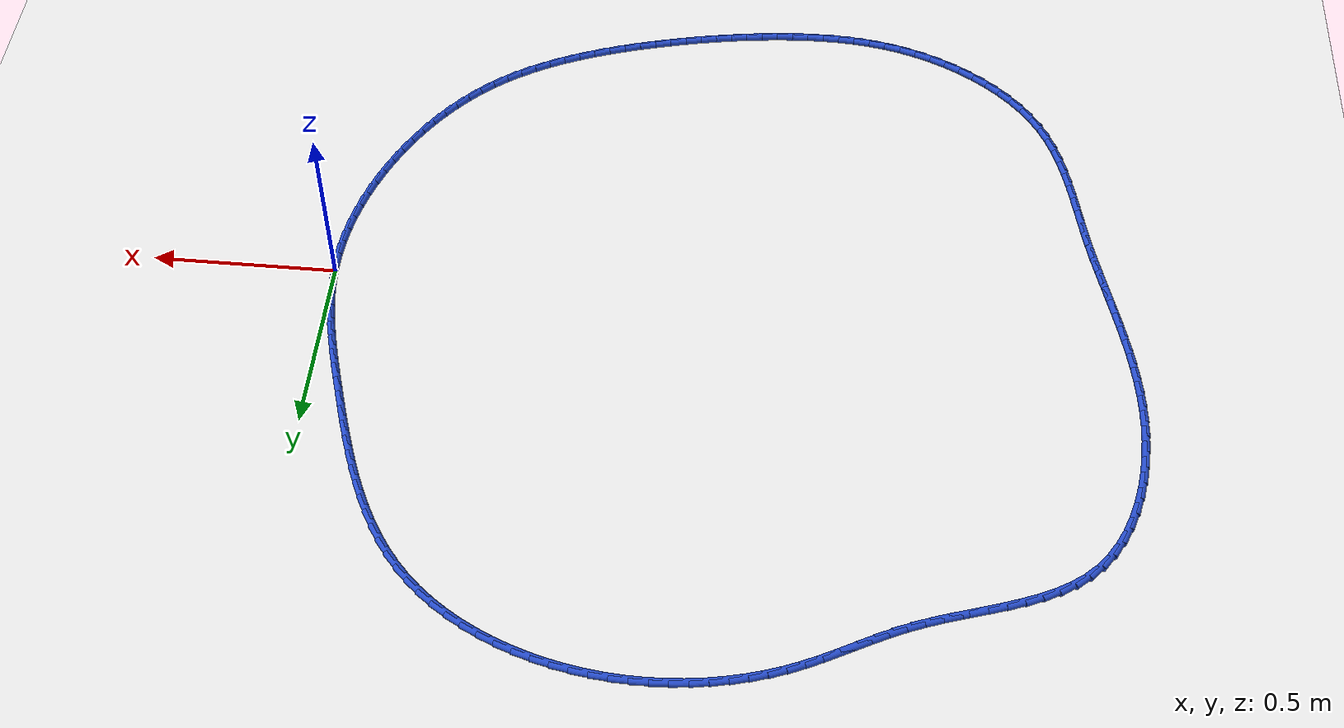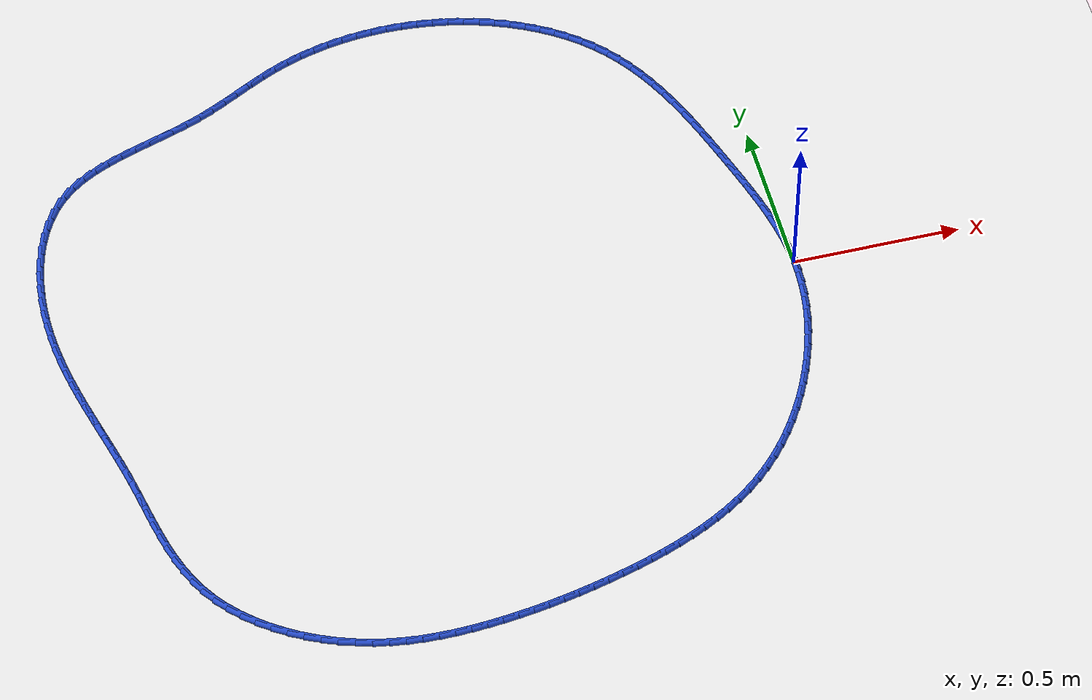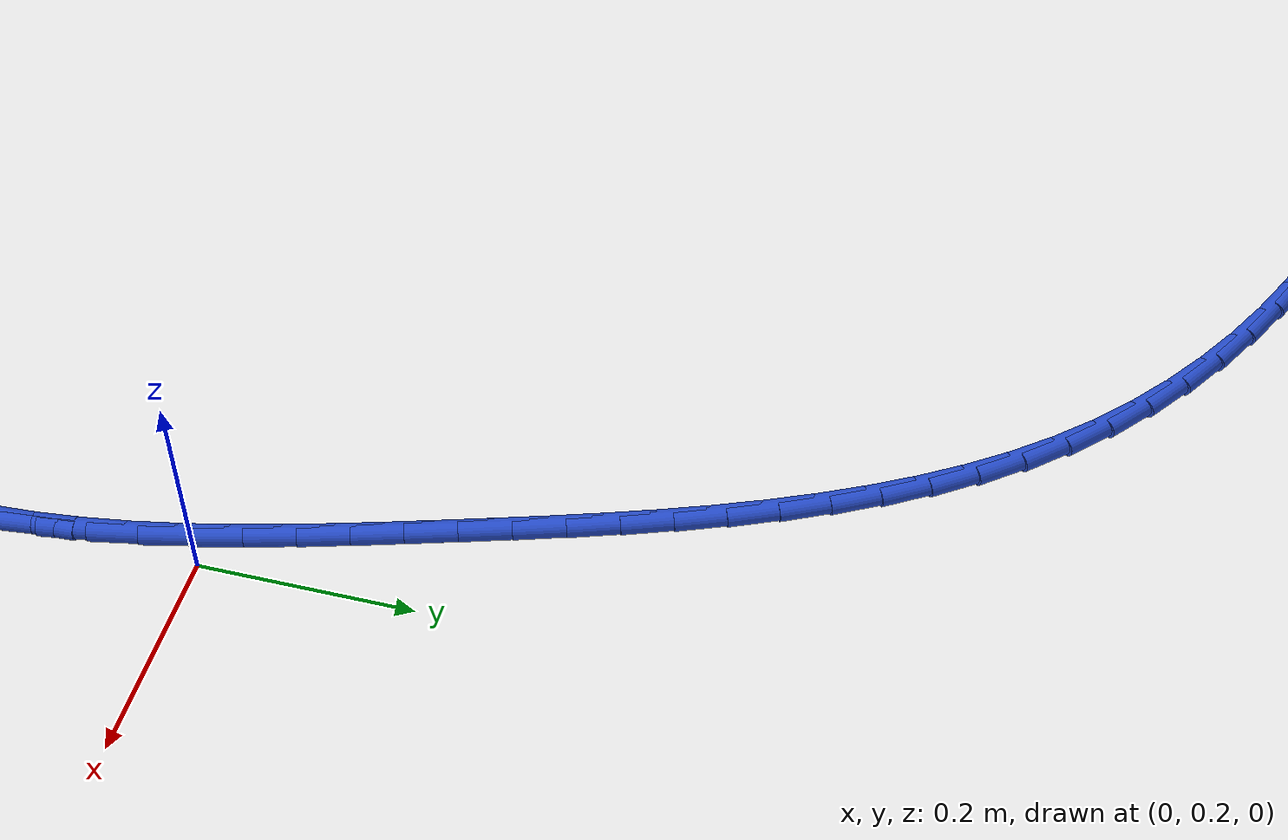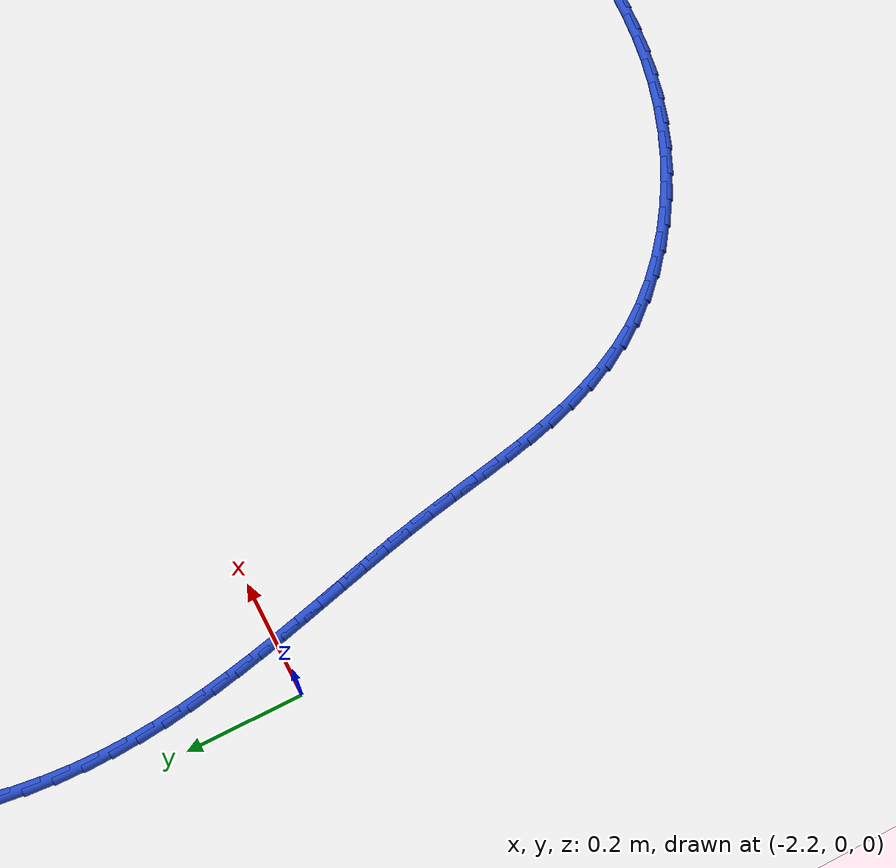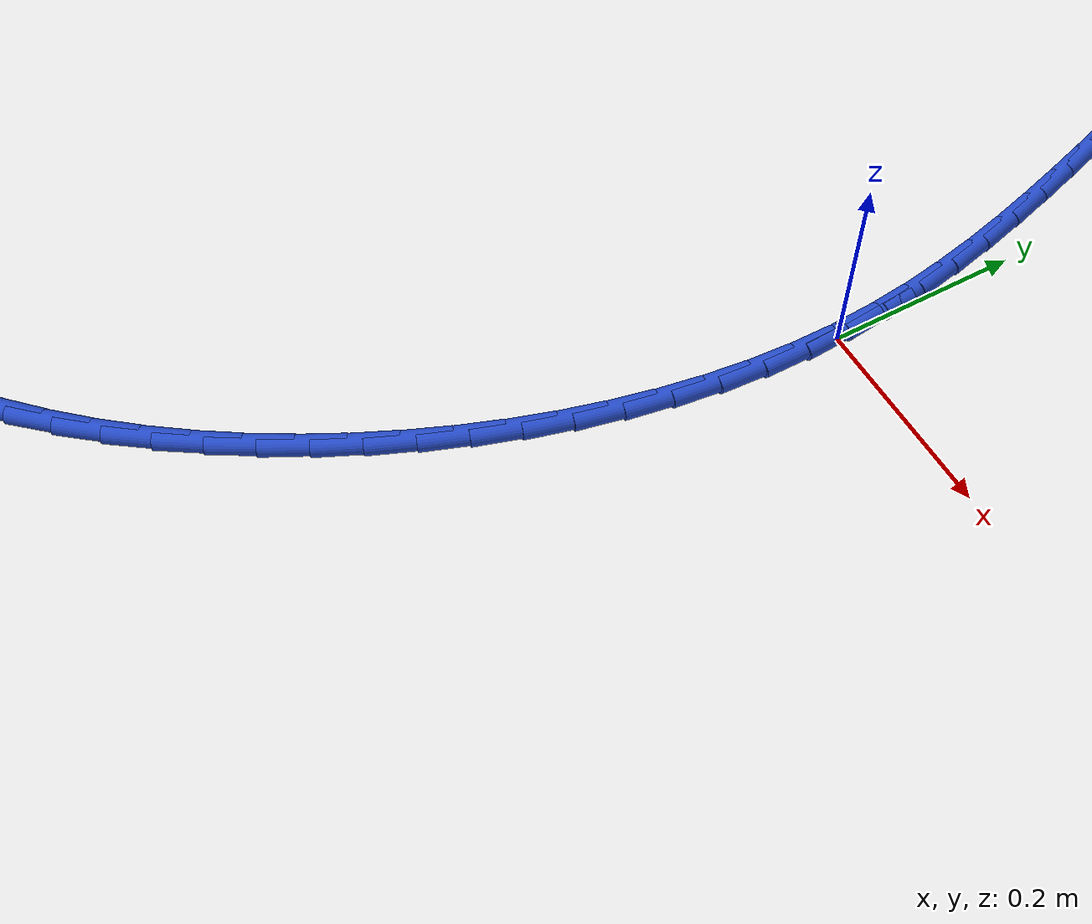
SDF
<sdf version="1.6">
 <world name="default">
  <light name="sun" type="directional">
   <pose>0 0 10 0 -0 0</pose>
   <diffuse>0.8 0.8 0.8 1</diffuse>
   <specular>0.2 0.2 0.2 1</specular>
   <attenuation>
    <range>1000</range>
    <constant>0.9</constant>
    <linear>0.01</linear>
    <quadratic>0.001</quadratic>
   </attenuation>
   <direction>-0.5 0.1 -0.9</direction>
  </light>
  <model name="ground_plane">
   <static>1</static>
   <link name="link">
    <collision name="collision">
     <geometry><plane><normal>0 0 1</normal><size>100 100</size></plane></geometry>
     <surface><friction><ode><mu>100</mu><mu2>50</mu2></ode></friction></surface>
    </collision>
    <visual name="visual">
     <cast_shadows>0</cast_shadows>
     <geometry><plane><normal>0 0 1</normal><size>100 100</size></plane></geometry>
     <material>
      <script><uri>file://media/materials/scripts/gazebo.material</uri><name>Gazebo/WhiteGlow</name></script>
     </material>
    </visual>
   </link>
  </model>
  <gravity>0 0 -9.8</gravity>
  <magnetic_field>6e-06 2.3e-05 -4.2e-05</magnetic_field>
  <atmosphere type="adiabatic"/>
  <physics name="default_physics" default="0" type="ode">
   <max_step_size>0.001</max_step_size>
   <real_time_factor>1</real_time_factor>
   <real_time_update_rate>1000</real_time_update_rate>
  </physics>
  <scene><ambient>0.4 0.4 0.4 1</ambient><background>0.7 0.7 0.7 1</background><shadows>1</shadows></scene>
  <spherical_coordinates>
   <surface_model>EARTH_WGS84</surface_model>
   <latitude_deg>0</latitude_deg>
   <longitude_deg>0</longitude_deg>
   <elevation>0</elevation>
   <heading_deg>0</heading_deg>
  </spherical_coordinates>
  <model name="line">
   <link name="link_0">
    <pose>5.204170427930421e-18 -2.0816681711721685e-16 0.01 0 1.57 -1.5151693214334319</pose>
    <collision name="collision">
     <geometry><cylinder><radius>0.01</radius><length>0.08</length></cylinder></geometry>
    </collision>
    <visual name="visual">
     <material>
      <script><name>Gazebo/Blue</name><uri>file://media/materials/scripts/gazebo.material</uri></script>
     </material>
     <geometry><cylinder><radius>0.01</radius><length>0.08</length></cylinder></geometry>
    </visual>
   </link>
   <link name="link_1">
    <pose>-0.0025199337838579176 0.0452538121353279 0.01 0 1.57 -1.4620434421293718</pose>
    <collision name="collision">
     <geometry><cylinder><radius>0.01</radius><length>0.08</length></cylinder></geometry>
    </collision>
    <visual name="visual">
     <material>
      <script><name>Gazebo/Blue</name><uri>file://media/materials/scripts/gazebo.material</uri></script>
     </material>
     <geometry><cylinder><radius>0.01</radius><length>0.08</length></cylinder></geometry>
    </visual>
   </link>
   <link name="link_2">
    <pose>-0.007439263140490313 0.0903093535602655 0.01 0 1.57 -1.4152869893317803</pose>
    <collision name="collision">
     <geometry><cylinder><radius>0.01</radius><length>0.08</length></cylinder></geometry>
    </collision>
    <visual name="visual">
     <material>
      <script><name>Gazebo/Blue</name><uri>file://media/materials/scripts/gazebo.material</uri></script>
     </material>
     <geometry><cylinder><radius>0.01</radius><length>0.08</length></cylinder></geometry>
    </visual>
   </link>
   <link name="link_3">
    <pose>-0.01447917036834315 0.13521383701764486 0.01 0 1.57 -1.375085294124724</pose>
    <collision name="collision">
     <geometry><cylinder><radius>0.01</radius><length>0.08</length></cylinder></geometry>
    </collision>
    <visual name="visual">
     <material>
      <script><name>Gazebo/Blue</name><uri>file://media/materials/scripts/gazebo.material</uri></script>
     </material>
     <geometry><cylinder><radius>0.01</radius><length>0.08</length></cylinder></geometry>
    </visual>
   </link>
   <link name="link_4">
    <pose>-0.02336083776586238 0.18001447525029807 0.01 0 1.57 -1.3414723681343954</pose>
    <collision name="collision">
     <geometry><cylinder><radius>0.01</radius><length>0.08</length></cylinder></geometry>
    </collision>
    <visual name="visual">
     <material>
      <script><name>Gazebo/Blue</name><uri>file://media/materials/scripts/gazebo.material</uri></script>
     </material>
     <geometry><cylinder><radius>0.01</radius><length>0.08</length></cylinder></geometry>
    </visual>
   </link>
   <link name="link_5">
    <pose>-0.03380544763149392 0.22475848100105741 0.01 0 1.57 -1.3143827715020846</pose>
    <collision name="collision">
     <geometry><cylinder><radius>0.01</radius><length>0.08</length></cylinder></geometry>
    </collision>
    <visual name="visual">
     <material>
      <script><name>Gazebo/Blue</name><uri>file://media/materials/scripts/gazebo.material</uri></script>
     </material>
     <geometry><cylinder><radius>0.01</radius><length>0.08</length></cylinder></geometry>
    </visual>
   </link>
   <link name="link_6">
    <pose>-0.04553418226368378 0.2694930670127552 0.01 0 1.57 -1.293696125618497</pose>
    <collision name="collision">
     <geometry><cylinder><radius>0.01</radius><length>0.08</length></cylinder></geometry>
    </collision>
    <visual name="visual">
     <material>
      <script><name>Gazebo/Blue</name><uri>file://media/materials/scripts/gazebo.material</uri></script>
     </material>
     <geometry><cylinder><radius>0.01</radius><length>0.08</length></cylinder></geometry>
    </visual>
   </link>
   <link name="link_7">
    <pose>-0.05826822396087787 0.31426544602822365 0.01 0 1.57 -1.2792717218021814</pose>
    <collision name="collision">
     <geometry><cylinder><radius>0.01</radius><length>0.08</length></cylinder></geometry>
    </collision>
    <visual name="visual">
     <material>
      <script><name>Gazebo/Blue</name><uri>file://media/materials/scripts/gazebo.material</uri></script>
     </material>
     <geometry><cylinder><radius>0.01</radius><length>0.08</length></cylinder></geometry>
    </visual>
   </link>
   <link name="link_8">
    <pose>-0.07172875502152215 0.3591228307902948 0.01 0 1.57 -1.2709730782702546</pose>
    <collision name="collision">
     <geometry><cylinder><radius>0.01</radius><length>0.08</length></cylinder></geometry>
    </collision>
    <visual name="visual">
     <material>
      <script><name>Gazebo/Blue</name><uri>file://media/materials/scripts/gazebo.material</uri></script>
     </material>
     <geometry><cylinder><radius>0.01</radius><length>0.08</length></cylinder></geometry>
    </visual>
   </link>
   <link name="link_9">
    <pose>-0.0856369577440626 0.4041124340418012 0.01 0 1.57 -1.267166131804651</pose>
    <collision name="collision">
     <geometry><cylinder><radius>0.01</radius><length>0.08</length></cylinder></geometry>
    </collision>
    <visual name="visual">
     <material>
      <script><name>Gazebo/Blue</name><uri>file://media/materials/scripts/gazebo.material</uri></script>
     </material>
     <geometry><cylinder><radius>0.01</radius><length>0.08</length></cylinder></geometry>
    </visual>
   </link>
   <link name="link_10">
    <pose>-0.0997791736986746 0.44924933096677455 0.01 0 1.57 -1.260565255090656</pose>
    <collision name="collision">
     <geometry><cylinder><radius>0.01</radius><length>0.08</length></cylinder></geometry>
    </collision>
    <visual name="visual">
     <material>
      <script><name>Gazebo/Blue</name><uri>file://media/materials/scripts/gazebo.material</uri></script>
     </material>
     <geometry><cylinder><radius>0.01</radius><length>0.08</length></cylinder></geometry>
    </visual>
   </link>
   <link name="link_11">
    <pose>-0.11425222481897394 0.4943954630405438 0.01 0 1.57 -1.2489957160301464</pose>
    <collision name="collision">
     <geometry><cylinder><radius>0.01</radius><length>0.08</length></cylinder></geometry>
    </collision>
    <visual name="visual">
     <material>
      <script><name>Gazebo/Blue</name><uri>file://media/materials/scripts/gazebo.material</uri></script>
     </material>
     <geometry><cylinder><radius>0.01</radius><length>0.08</length></cylinder></geometry>
    </visual>
   </link>
   <link name="link_12">
    <pose>-0.12924530864813347 0.5393672106616327 0.01 0 1.57 -1.2323748984446634</pose>
    <collision name="collision">
     <geometry><cylinder><radius>0.01</radius><length>0.08</length></cylinder></geometry>
    </collision>
    <visual name="visual">
     <material>
      <script><name>Gazebo/Blue</name><uri>file://media/materials/scripts/gazebo.material</uri></script>
     </material>
     <geometry><cylinder><radius>0.01</radius><length>0.08</length></cylinder></geometry>
    </visual>
   </link>
   <link name="link_13">
    <pose>-0.14494763812015357 0.5839809466375709 0.01 0 1.57 -1.2105593465376678</pose>
    <collision name="collision">
     <geometry><cylinder><radius>0.01</radius><length>0.08</length></cylinder></geometry>
    </collision>
    <visual name="visual">
     <material>
      <script><name>Gazebo/Blue</name><uri>file://media/materials/scripts/gazebo.material</uri></script>
     </material>
     <geometry><cylinder><radius>0.01</radius><length>0.08</length></cylinder></geometry>
    </visual>
   </link>
   <link name="link_14">
    <pose>-0.16154842616903484 0.6280530437758886 0.01 0 1.57 -1.1833540880014557</pose>
    <collision name="collision">
     <geometry><cylinder><radius>0.01</radius><length>0.08</length></cylinder></geometry>
    </collision>
    <visual name="visual">
     <material>
      <script><name>Gazebo/Blue</name><uri>file://media/materials/scripts/gazebo.material</uri></script>
     </material>
     <geometry><cylinder><radius>0.01</radius><length>0.08</length></cylinder></geometry>
    </visual>
   </link>
   <link name="link_15">
    <pose>-0.17923688572877752 0.6713998748841147 0.01 0 1.57 -1.150526699200057</pose>
    <collision name="collision">
     <geometry><cylinder><radius>0.01</radius><length>0.08</length></cylinder></geometry>
    </collision>
    <visual name="visual">
     <material>
      <script><name>Gazebo/Blue</name><uri>file://media/materials/scripts/gazebo.material</uri></script>
     </material>
     <geometry><cylinder><radius>0.01</radius><length>0.08</length></cylinder></geometry>
    </visual>
   </link>
   <link name="link_16">
    <pose>-0.19820222973338225 0.7138378127697798 0.01 0 1.57 -1.111827931628242</pose>
    <collision name="collision">
     <geometry><cylinder><radius>0.01</radius><length>0.08</length></cylinder></geometry>
    </collision>
    <visual name="visual">
     <material>
      <script><name>Gazebo/Blue</name><uri>file://media/materials/scripts/gazebo.material</uri></script>
     </material>
     <geometry><cylinder><radius>0.01</radius><length>0.08</length></cylinder></geometry>
    </visual>
   </link>
   <link name="link_17">
    <pose>-0.21863367111684948 0.7551832302404131 0.01 0 1.57 -1.0670213642709678</pose>
    <collision name="collision">
     <geometry><cylinder><radius>0.01</radius><length>0.08</length></cylinder></geometry>
    </collision>
    <visual name="visual">
     <material>
      <script><name>Gazebo/Blue</name><uri>file://media/materials/scripts/gazebo.material</uri></script>
     </material>
     <geometry><cylinder><radius>0.01</radius><length>0.08</length></cylinder></geometry>
    </visual>
   </link>
   <link name="link_18">
    <pose>-0.24072042281317957 0.7952525001035449 0.01 0 1.57 -1.0159243109853648</pose>
    <collision name="collision">
     <geometry><cylinder><radius>0.01</radius><length>0.08</length></cylinder></geometry>
    </collision>
    <visual name="visual">
     <material>
      <script><name>Gazebo/Blue</name><uri>file://media/materials/scripts/gazebo.material</uri></script>
     </material>
     <geometry><cylinder><radius>0.01</radius><length>0.08</length></cylinder></geometry>
    </visual>
   </link>
   <link name="link_19">
    <pose>-0.2646516977563731 0.8338619951667048 0.01 0 1.57 -0.9584609441706166</pose>
    <collision name="collision">
     <geometry><cylinder><radius>0.01</radius><length>0.08</length></cylinder></geometry>
    </collision>
    <visual name="visual">
     <material>
      <script><name>Gazebo/Blue</name><uri>file://media/materials/scripts/gazebo.material</uri></script>
     </material>
     <geometry><cylinder><radius>0.01</radius><length>0.08</length></cylinder></geometry>
    </visual>
   </link>
   <link name="link_20">
    <pose>-0.2906167088804304 0.870828088237422 0.01 0 1.57 -0.8947256941530735</pose>
    <collision name="collision">
     <geometry><cylinder><radius>0.01</radius><length>0.08</length></cylinder></geometry>
    </collision>
    <visual name="visual">
     <material>
      <script><name>Gazebo/Blue</name><uri>file://media/materials/scripts/gazebo.material</uri></script>
     </material>
     <geometry><cylinder><radius>0.01</radius><length>0.08</length></cylinder></geometry>
    </visual>
   </link>
   <link name="link_21">
    <pose>-0.31880466911935224 0.9059671521232275 0.01 0 1.57 -0.825052313663948</pose>
    <collision name="collision">
     <geometry><cylinder><radius>0.01</radius><length>0.08</length></cylinder></geometry>
    </collision>
    <visual name="visual">
     <material>
      <script><name>Gazebo/Blue</name><uri>file://media/materials/scripts/gazebo.material</uri></script>
     </material>
     <geometry><cylinder><radius>0.01</radius><length>0.08</length></cylinder></geometry>
    </visual>
   </link>
   <link name="link_22">
    <pose>-0.34940469139362323 0.9390955980660239 0.01 0 1.57 -0.7520608713326664</pose>
    <collision name="collision">
     <geometry><cylinder><radius>0.01</radius><length>0.08</length></cylinder></geometry>
    </collision>
    <visual name="visual">
     <material>
      <script><name>Gazebo/Blue</name><uri>file://media/materials/scripts/gazebo.material</uri></script>
     </material>
     <geometry><cylinder><radius>0.01</radius><length>0.08</length></cylinder></geometry>
    </visual>
   </link>
   <link name="link_23">
    <pose>-0.3825119835709244 0.9700659242496591 0.01 0 1.57 -0.6818319209711832</pose>
    <collision name="collision">
     <geometry><cylinder><radius>0.01</radius><length>0.08</length></cylinder></geometry>
    </collision>
    <visual name="visual">
     <material>
      <script><name>Gazebo/Blue</name><uri>file://media/materials/scripts/gazebo.material</uri></script>
     </material>
     <geometry><cylinder><radius>0.01</radius><length>0.08</length></cylinder></geometry>
    </visual>
   </link>
   <link name="link_24">
    <pose>-0.417953553534305 0.9988336959133234 0.01 0 1.57 -0.6151861687530391</pose>
    <collision name="collision">
     <geometry><cylinder><radius>0.01</radius><length>0.08</length></cylinder></geometry>
    </collision>
    <visual name="visual">
     <material>
      <script><name>Gazebo/Blue</name><uri>file://media/materials/scripts/gazebo.material</uri></script>
     </material>
     <geometry><cylinder><radius>0.01</radius><length>0.08</length></cylinder></geometry>
    </visual>
   </link>
   <link name="link_25">
    <pose>-0.4555088378247184 1.025372759572978 0.01 0 1.57 -0.5518065119680559</pose>
    <collision name="collision">
     <geometry><cylinder><radius>0.01</radius><length>0.08</length></cylinder></geometry>
    </collision>
    <visual name="visual">
     <material>
      <script><name>Gazebo/Blue</name><uri>file://media/materials/scripts/gazebo.material</uri></script>
     </material>
     <geometry><cylinder><radius>0.01</radius><length>0.08</length></cylinder></geometry>
    </visual>
   </link>
   <link name="link_26">
    <pose>-0.4949572729831174 1.0496569617445828 0.01 0 1.57 -0.4913190457030457</pose>
    <collision name="collision">
     <geometry><cylinder><radius>0.01</radius><length>0.08</length></cylinder></geometry>
    </collision>
    <visual name="visual">
     <material>
      <script><name>Gazebo/Blue</name><uri>file://media/materials/scripts/gazebo.material</uri></script>
     </material>
     <geometry><cylinder><radius>0.01</radius><length>0.08</length></cylinder></geometry>
    </visual>
   </link>
   <link name="link_27">
    <pose>-0.5360782955504556 1.0716601489440998 0.01 0 1.57 -0.433315966512853</pose>
    <collision name="collision">
     <geometry><cylinder><radius>0.01</radius><length>0.08</length></cylinder></geometry>
    </collision>
    <visual name="visual">
     <material>
      <script><name>Gazebo/Blue</name><uri>file://media/materials/scripts/gazebo.material</uri></script>
     </material>
     <geometry><cylinder><radius>0.01</radius><length>0.08</length></cylinder></geometry>
    </visual>
   </link>
   <link name="link_28">
    <pose>-0.5786513420676855 1.0913561676874886 0.01 0 1.57 -0.3773712681958708</pose>
    <collision name="collision">
     <geometry><cylinder><radius>0.01</radius><length>0.08</length></cylinder></geometry>
    </collision>
    <visual name="visual">
     <material>
      <script><name>Gazebo/Blue</name><uri>file://media/materials/scripts/gazebo.material</uri></script>
     </material>
     <geometry><cylinder><radius>0.01</radius><length>0.08</length></cylinder></geometry>
    </visual>
   </link>
   <link name="link_29">
    <pose>-0.6224558490757609 1.1087188644907104 0.01 0 1.57 -0.32305039196189217</pose>
    <collision name="collision">
     <geometry><cylinder><radius>0.01</radius><length>0.08</length></cylinder></geometry>
    </collision>
    <visual name="visual">
     <material>
      <script><name>Gazebo/Blue</name><uri>file://media/materials/scripts/gazebo.material</uri></script>
     </material>
     <geometry><cylinder><radius>0.01</radius><length>0.08</length></cylinder></geometry>
    </visual>
   </link>
   <link name="link_30">
    <pose>-0.6672712531156345 1.1237220858697259 0.01 0 1.57 -0.26991513958716984</pose>
    <collision name="collision">
     <geometry><cylinder><radius>0.01</radius><length>0.08</length></cylinder></geometry>
    </collision>
    <visual name="visual">
     <material>
      <script><name>Gazebo/Blue</name><uri>file://media/materials/scripts/gazebo.material</uri></script>
     </material>
     <geometry><cylinder><radius>0.01</radius><length>0.08</length></cylinder></geometry>
    </visual>
   </link>
   <link name="link_31">
    <pose>-0.7128769907282595 1.1363396783404953 0.01 0 1.57 -0.21754101176765656</pose>
    <collision name="collision">
     <geometry><cylinder><radius>0.01</radius><length>0.08</length></cylinder></geometry>
    </collision>
    <visual name="visual">
     <material>
      <script><name>Gazebo/Blue</name><uri>file://media/materials/scripts/gazebo.material</uri></script>
     </material>
     <geometry><cylinder><radius>0.01</radius><length>0.08</length></cylinder></geometry>
    </visual>
   </link>
   <link name="link_32">
    <pose>-0.7590551185782016 1.1465468401750623 0.01 0 1.57 -0.1658233409956092</pose>
    <collision name="collision">
     <geometry><cylinder><radius>0.01</radius><length>0.08</length></cylinder></geometry>
    </collision>
    <visual name="visual">
     <material>
      <script><name>Gazebo/Blue</name><uri>file://media/materials/scripts/gazebo.material</uri></script>
     </material>
     <geometry><cylinder><radius>0.01</radius><length>0.08</length></cylinder></geometry>
    </visual>
   </link>
   <link name="link_33">
    <pose>-0.8056329351589436 1.1543421104974472 0.01 0 1.57 -0.11480630914273515</pose>
    <collision name="collision">
     <geometry><cylinder><radius>0.01</radius><length>0.08</length></cylinder></geometry>
    </collision>
    <visual name="visual">
     <material>
      <script><name>Gazebo/Blue</name><uri>file://media/materials/scripts/gazebo.material</uri></script>
     </material>
     <geometry><cylinder><radius>0.01</radius><length>0.08</length></cylinder></geometry>
    </visual>
   </link>
   <link name="link_34">
    <pose>-0.852475937619082 1.159743735618054 0.01 0 1.57 -0.06434642894121052</pose>
    <collision name="collision">
     <geometry><cylinder><radius>0.01</radius><length>0.08</length></cylinder></geometry>
    </collision>
    <visual name="visual">
     <material>
      <script><name>Gazebo/Blue</name><uri>file://media/materials/scripts/gazebo.material</uri></script>
     </material>
     <geometry><cylinder><radius>0.01</radius><length>0.08</length></cylinder></geometry>
    </visual>
   </link>
   <link name="link_35">
    <pose>-0.8994508219390371 1.1627705803403234 0.01 0 1.57 -0.014282181406986642</pose>
    <collision name="collision">
     <geometry><cylinder><radius>0.01</radius><length>0.08</length></cylinder></geometry>
    </collision>
    <visual name="visual">
     <material>
      <script><name>Gazebo/Blue</name><uri>file://media/materials/scripts/gazebo.material</uri></script>
     </material>
     <geometry><cylinder><radius>0.01</radius><length>0.08</length></cylinder></geometry>
    </visual>
   </link>
   <link name="link_36">
    <pose>-0.9464242840992299 1.1634415094676955 0.01 0 1.57 0.03555645625680086</pose>
    <collision name="collision">
     <geometry><cylinder><radius>0.01</radius><length>0.08</length></cylinder></geometry>
    </collision>
    <visual name="visual">
     <material>
      <script><name>Gazebo/Blue</name><uri>file://media/materials/scripts/gazebo.material</uri></script>
     </material>
     <geometry><cylinder><radius>0.01</radius><length>0.08</length></cylinder></geometry>
    </visual>
   </link>
   <link name="link_37">
    <pose>-0.9932630200800812 1.1617753878036123 0.01 0 1.57 0.0853461213029682</pose>
    <collision name="collision">
     <geometry><cylinder><radius>0.01</radius><length>0.08</length></cylinder></geometry>
    </collision>
    <visual name="visual">
     <material>
      <script><name>Gazebo/Blue</name><uri>file://media/materials/scripts/gazebo.material</uri></script>
     </material>
     <geometry><cylinder><radius>0.01</radius><length>0.08</length></cylinder></geometry>
    </visual>
   </link>
   <link name="link_38">
    <pose>-1.0398337258620107 1.1577910801515126 0.01 0 1.57 0.1352684000227447</pose>
    <collision name="collision">
     <geometry><cylinder><radius>0.01</radius><length>0.08</length></cylinder></geometry>
    </collision>
    <visual name="visual">
     <material>
      <script><name>Gazebo/Blue</name><uri>file://media/materials/scripts/gazebo.material</uri></script>
     </material>
     <geometry><cylinder><radius>0.01</radius><length>0.08</length></cylinder></geometry>
    </visual>
   </link>
   <link name="link_39">
    <pose>-1.0860030974254402 1.1515074513148382 0.01 0 1.57 0.18550825141826252</pose>
    <collision name="collision">
     <geometry><cylinder><radius>0.01</radius><length>0.08</length></cylinder></geometry>
    </collision>
    <visual name="visual">
     <material>
      <script><name>Gazebo/Blue</name><uri>file://media/materials/scripts/gazebo.material</uri></script>
     </material>
     <geometry><cylinder><radius>0.01</radius><length>0.08</length></cylinder></geometry>
    </visual>
   </link>
   <link name="link_40">
    <pose>-1.1316378307507895 1.1429433660970292 0.01 0 1.57 0.2362523699049097</pose>
    <collision name="collision">
     <geometry><cylinder><radius>0.01</radius><length>0.08</length></cylinder></geometry>
    </collision>
    <visual name="visual">
     <material>
      <script><name>Gazebo/Blue</name><uri>file://media/materials/scripts/gazebo.material</uri></script>
     </material>
     <geometry><cylinder><radius>0.01</radius><length>0.08</length></cylinder></geometry>
    </visual>
   </link>
   <link name="link_41">
    <pose>-1.17660462181848 1.1321176893015266 0.01 0 1.57 0.28768732393313073</pose>
    <collision name="collision">
     <geometry><cylinder><radius>0.01</radius><length>0.08</length></cylinder></geometry>
    </collision>
    <visual name="visual">
     <material>
      <script><name>Gazebo/Blue</name><uri>file://media/materials/scripts/gazebo.material</uri></script>
     </material>
     <geometry><cylinder><radius>0.01</radius><length>0.08</length></cylinder></geometry>
    </visual>
   </link>
   <link name="link_42">
    <pose>-1.2207701666089317 1.1190492857317702 0.01 0 1.57 0.33999729677290624</pose>
    <collision name="collision">
     <geometry><cylinder><radius>0.01</radius><length>0.08</length></cylinder></geometry>
    </collision>
    <visual name="visual">
     <material>
      <script><name>Gazebo/Blue</name><uri>file://media/materials/scripts/gazebo.material</uri></script>
     </material>
     <geometry><cylinder><radius>0.01</radius><length>0.08</length></cylinder></geometry>
    </visual>
   </link>
   <link name="link_43">
    <pose>-1.2640011611025652 1.1037570201912015 0.01 0 1.57 0.3932344755952296</pose>
    <collision name="collision">
     <geometry><cylinder><radius>0.01</radius><length>0.08</length></cylinder></geometry>
    </collision>
    <visual name="visual">
     <material>
      <script><name>Gazebo/Blue</name><uri>file://media/materials/scripts/gazebo.material</uri></script>
     </material>
     <geometry><cylinder><radius>0.01</radius><length>0.08</length></cylinder></geometry>
    </visual>
   </link>
   <link name="link_44">
    <pose>-1.3061682742316838 1.0862643747307368 0.01 0 1.57 0.4408505728273881</pose>
    <collision name="collision">
     <geometry><cylinder><radius>0.01</radius><length>0.08</length></cylinder></geometry>
    </collision>
    <visual name="visual">
     <material>
      <script><name>Gazebo/Blue</name><uri>file://media/materials/scripts/gazebo.material</uri></script>
     </material>
     <geometry><cylinder><radius>0.01</radius><length>0.08</length></cylinder></geometry>
    </visual>
   </link>
   <link name="link_45">
    <pose>-1.3473485630042519 1.0668346895344205 0.01 0 1.57 0.47277220237916373</pose>
    <collision name="collision">
     <geometry><cylinder><radius>0.01</radius><length>0.08</length></cylinder></geometry>
    </collision>
    <visual name="visual">
     <material>
      <script><name>Gazebo/Blue</name><uri>file://media/materials/scripts/gazebo.material</uri></script>
     </material>
     <geometry><cylinder><radius>0.01</radius><length>0.08</length></cylinder></geometry>
    </visual>
   </link>
   <link name="link_46">
    <pose>-1.387921834271943 1.0460831517235993 0.01 0 1.57 0.48801485386211624</pose>
    <collision name="collision">
     <geometry><cylinder><radius>0.01</radius><length>0.08</length></cylinder></geometry>
    </collision>
    <visual name="visual">
     <material>
      <script><name>Gazebo/Blue</name><uri>file://media/materials/scripts/gazebo.material</uri></script>
     </material>
     <geometry><cylinder><radius>0.01</radius><length>0.08</length></cylinder></geometry>
    </visual>
   </link>
   <link name="link_47">
    <pose>-1.4282920315184382 1.0246529993013114 0.01 0 1.57 0.4866437018627024</pose>
    <collision name="collision">
     <geometry><cylinder><radius>0.01</radius><length>0.08</length></cylinder></geometry>
    </collision>
    <visual name="visual">
     <material>
      <script><name>Gazebo/Blue</name><uri>file://media/materials/scripts/gazebo.material</uri></script>
     </material>
     <geometry><cylinder><radius>0.01</radius><length>0.08</length></cylinder></geometry>
    </visual>
   </link>
   <link name="link_48">
    <pose>-1.4688630982274207 1.0031874702705967 0.01 0 1.57 0.4688743670649296</pose>
    <collision name="collision">
     <geometry><cylinder><radius>0.01</radius><length>0.08</length></cylinder></geometry>
    </collision>
    <visual name="visual">
     <material>
      <script><name>Gazebo/Blue</name><uri>file://media/materials/scripts/gazebo.material</uri></script>
     </material>
     <geometry><cylinder><radius>0.01</radius><length>0.08</length></cylinder></geometry>
    </visual>
   </link>
   <link name="link_49">
    <pose>-1.5100389778825702 0.9823298026344933 0.01 0 1.57 0.4350766351396224</pose>
    <collision name="collision">
     <geometry><cylinder><radius>0.01</radius><length>0.08</length></cylinder></geometry>
    </collision>
    <visual name="visual">
     <material>
      <script><name>Gazebo/Blue</name><uri>file://media/materials/scripts/gazebo.material</uri></script>
     </material>
     <geometry><cylinder><radius>0.01</radius><length>0.08</length></cylinder></geometry>
    </visual>
   </link>
   <link name="link_50">
    <pose>-1.5522236139675696 0.9627232343960409 0.01 0 1.57 0.3879110520418586</pose>
    <collision name="collision">
     <geometry><cylinder><radius>0.01</radius><length>0.08</length></cylinder></geometry>
    </collision>
    <visual name="visual">
     <material>
      <script><name>Gazebo/Blue</name><uri>file://media/materials/scripts/gazebo.material</uri></script>
     </material>
     <geometry><cylinder><radius>0.01</radius><length>0.08</length></cylinder></geometry>
    </visual>
   </link>
   <link name="link_51">
    <pose>-1.5957638398927176 0.9449320407488593 0.01 0 1.57 0.34717667763188276</pose>
    <collision name="collision">
     <geometry><cylinder><radius>0.01</radius><length>0.08</length></cylinder></geometry>
    </collision>
    <visual name="visual">
     <material>
      <script><name>Gazebo/Blue</name><uri>file://media/materials/scripts/gazebo.material</uri></script>
     </material>
     <geometry><cylinder><radius>0.01</radius><length>0.08</length></cylinder></geometry>
    </visual>
   </link>
   <link name="link_52">
    <pose>-1.6404569217688876 0.9287606418319624 0.01 0 1.57 0.3229288441164636</pose>
    <collision name="collision">
     <geometry><cylinder><radius>0.01</radius><length>0.08</length></cylinder></geometry>
    </collision>
    <visual name="visual">
     <material>
      <script><name>Gazebo/Blue</name><uri>file://media/materials/scripts/gazebo.material</uri></script>
     </material>
     <geometry><cylinder><radius>0.01</radius><length>0.08</length></cylinder></geometry>
    </visual>
   </link>
   <link name="link_53">
    <pose>-1.6857932475800588 0.9135891550718267 0.01 0 1.57 0.3146183898904794</pose>
    <collision name="collision">
     <geometry><cylinder><radius>0.01</radius><length>0.08</length></cylinder></geometry>
    </collision>
    <visual name="visual">
     <material>
      <script><name>Gazebo/Blue</name><uri>file://media/materials/scripts/gazebo.material</uri></script>
     </material>
     <geometry><cylinder><radius>0.01</radius><length>0.08</length></cylinder></geometry>
    </visual>
   </link>
   <link name="link_54">
    <pose>-1.7312598614935808 0.8987930745922521 0.01 0 1.57 0.32209383492785537</pose>
    <collision name="collision">
     <geometry><cylinder><radius>0.01</radius><length>0.08</length></cylinder></geometry>
    </collision>
    <visual name="visual">
     <material>
      <script><name>Gazebo/Blue</name><uri>file://media/materials/scripts/gazebo.material</uri></script>
     </material>
     <geometry><cylinder><radius>0.01</radius><length>0.08</length></cylinder></geometry>
    </visual>
   </link>
   <link name="link_55">
    <pose>-1.7763438076768037 0.8837478945170378 0.01 0 1.57 0.34577572491099423</pose>
    <collision name="collision">
     <geometry><cylinder><radius>0.01</radius><length>0.08</length></cylinder></geometry>
    </collision>
    <visual name="visual">
     <material>
      <script><name>Gazebo/Blue</name><uri>file://media/materials/scripts/gazebo.material</uri></script>
     </material>
     <geometry><cylinder><radius>0.01</radius><length>0.08</length></cylinder></geometry>
    </visual>
   </link>
   <link name="link_56">
    <pose>-1.8205321302970774 0.8678291089699842 0.01 0 1.57 0.3866373767102883</pose>
    <collision name="collision">
     <geometry><cylinder><radius>0.01</radius><length>0.08</length></cylinder></geometry>
    </collision>
    <visual name="visual">
     <material>
      <script><name>Gazebo/Blue</name><uri>file://media/materials/scripts/gazebo.material</uri></script>
     </material>
     <geometry><cylinder><radius>0.01</radius><length>0.08</length></cylinder></geometry>
    </visual>
   </link>
   <link name="link_57">
    <pose>-1.8633118735217535 0.8504122120748908 0.01 0 1.57 0.446078300359558</pose>
    <collision name="collision">
     <geometry><cylinder><radius>0.01</radius><length>0.08</length></cylinder></geometry>
    </collision>
    <visual name="visual">
     <material>
      <script><name>Gazebo/Blue</name><uri>file://media/materials/scripts/gazebo.material</uri></script>
     </material>
     <geometry><cylinder><radius>0.01</radius><length>0.08</length></cylinder></geometry>
    </visual>
   </link>
   <link name="link_58">
    <pose>-1.9041700815181815 0.8308726979555571 0.01 0 1.57 0.5256009580645761</pose>
    <collision name="collision">
     <geometry><cylinder><radius>0.01</radius><length>0.08</length></cylinder></geometry>
    </collision>
    <visual name="visual">
     <material>
      <script><name>Gazebo/Blue</name><uri>file://media/materials/scripts/gazebo.material</uri></script>
     </material>
     <geometry><cylinder><radius>0.01</radius><length>0.08</length></cylinder></geometry>
    </visual>
   </link>
   <link name="link_59">
    <pose>-1.9425937984537116 0.8085860607357833 0.01 0 1.57 0.626161164494511</pose>
    <collision name="collision">
     <geometry><cylinder><radius>0.01</radius><length>0.08</length></cylinder></geometry>
    </collision>
    <visual name="visual">
     <material>
      <script><name>Gazebo/Blue</name><uri>file://media/materials/scripts/gazebo.material</uri></script>
     </material>
     <geometry><cylinder><radius>0.01</radius><length>0.08</length></cylinder></geometry>
    </visual>
   </link>
   <link name="link_60">
    <pose>-1.9780700684956938 0.782927794539369 0.01 0 1.57 0.7469293131444559</pose>
    <collision name="collision">
     <geometry><cylinder><radius>0.01</radius><length>0.08</length></cylinder></geometry>
    </collision>
    <visual name="visual">
     <material>
      <script><name>Gazebo/Blue</name><uri>file://media/materials/scripts/gazebo.material</uri></script>
     </material>
     <geometry><cylinder><radius>0.01</radius><length>0.08</length></cylinder></geometry>
    </visual>
   </link>
   <link name="link_61">
    <pose>-2.0100902542642767 0.7532810361025792 0.01 0 1.57 0.873952563246763</pose>
    <collision name="collision">
     <geometry><cylinder><radius>0.01</radius><length>0.08</length></cylinder></geometry>
    </collision>
    <visual name="visual">
     <material>
      <script><name>Gazebo/Blue</name><uri>file://media/materials/scripts/gazebo.material</uri></script>
     </material>
     <geometry><cylinder><radius>0.01</radius><length>0.08</length></cylinder></geometry>
    </visual>
   </link>
   <link name="link_62">
    <pose>-2.03839172720948 0.7194642980330835 0.01 0 1.57 0.9885404855331816</pose>
    <collision name="collision">
     <geometry><cylinder><radius>0.01</radius><length>0.08</length></cylinder></geometry>
    </collision>
    <visual name="visual">
     <material>
      <script><name>Gazebo/Blue</name><uri>file://media/materials/scripts/gazebo.material</uri></script>
     </material>
     <geometry><cylinder><radius>0.01</radius><length>0.08</length></cylinder></geometry>
    </visual>
   </link>
   <link name="link_63">
    <pose>-2.063085825758061 0.6819579236478726 0.01 0 1.57 1.089612237796458</pose>
    <collision name="collision">
     <geometry><cylinder><radius>0.01</radius><length>0.08</length></cylinder></geometry>
    </collision>
    <visual name="visual">
     <material>
      <script><name>Gazebo/Blue</name><uri>file://media/materials/scripts/gazebo.material</uri></script>
     </material>
     <geometry><cylinder><radius>0.01</radius><length>0.08</length></cylinder></geometry>
    </visual>
   </link>
   <link name="link_64">
    <pose>-2.0843152139395604 0.6412976949716238 0.01 0 1.57 1.1784743448816928</pose>
    <collision name="collision">
     <geometry><cylinder><radius>0.01</radius><length>0.08</length></cylinder></geometry>
    </collision>
    <visual name="visual">
     <material>
      <script><name>Gazebo/Blue</name><uri>file://media/materials/scripts/gazebo.material</uri></script>
     </material>
     <geometry><cylinder><radius>0.01</radius><length>0.08</length></cylinder></geometry>
    </visual>
   </link>
   <link name="link_65">
    <pose>-2.1022225557835137 0.5980193940290159 0.01 0 1.57 1.2568482442506064</pose>
    <collision name="collision">
     <geometry><cylinder><radius>0.01</radius><length>0.08</length></cylinder></geometry>
    </collision>
    <visual name="visual">
     <material>
      <script><name>Gazebo/Blue</name><uri>file://media/materials/scripts/gazebo.material</uri></script>
     </material>
     <geometry><cylinder><radius>0.01</radius><length>0.08</length></cylinder></geometry>
    </visual>
   </link>
   <link name="link_66">
    <pose>-2.1169505153194628 0.5526588028447271 0.01 0 1.57 1.3265307612237203</pose>
    <collision name="collision">
     <geometry><cylinder><radius>0.01</radius><length>0.08</length></cylinder></geometry>
    </collision>
    <visual name="visual">
     <material>
      <script><name>Gazebo/Blue</name><uri>file://media/materials/scripts/gazebo.material</uri></script>
     </material>
     <geometry><cylinder><radius>0.01</radius><length>0.08</length></cylinder></geometry>
    </visual>
   </link>
   <link name="link_67">
    <pose>-2.128641756576944 0.5057517034434357 0.01 0 1.57 1.3892291839897848</pose>
    <collision name="collision">
     <geometry><cylinder><radius>0.01</radius><length>0.08</length></cylinder></geometry>
    </collision>
    <visual name="visual">
     <material>
      <script><name>Gazebo/Blue</name><uri>file://media/materials/scripts/gazebo.material</uri></script>
     </material>
     <geometry><cylinder><radius>0.01</radius><length>0.08</length></cylinder></geometry>
    </visual>
   </link>
   <link name="link_68">
    <pose>-2.1374389435854986 0.4578338778498205 0.01 0 1.57 1.4465084641314208</pose>
    <collision name="collision">
     <geometry><cylinder><radius>0.01</radius><length>0.08</length></cylinder></geometry>
    </collision>
    <visual name="visual">
     <material>
      <script><name>Gazebo/Blue</name><uri>file://media/materials/scripts/gazebo.material</uri></script>
     </material>
     <geometry><cylinder><radius>0.01</radius><length>0.08</length></cylinder></geometry>
    </visual>
   </link>
   <link name="link_69">
    <pose>-2.143484740374664 0.4094411080885597 0.01 0 1.57 1.499801975492854</pose>
    <collision name="collision">
     <geometry><cylinder><radius>0.01</radius><length>0.08</length></cylinder></geometry>
    </collision>
    <visual name="visual">
     <material>
      <script><name>Gazebo/Blue</name><uri>file://media/materials/scripts/gazebo.material</uri></script>
     </material>
     <geometry><cylinder><radius>0.01</radius><length>0.08</length></cylinder></geometry>
    </visual>
   </link>
   <link name="link_70">
    <pose>-2.1469218109739794 0.3611091761843317 0.01 0 1.57 1.5504005766205977</pose>
    <collision name="collision">
     <geometry><cylinder><radius>0.01</radius><length>0.08</length></cylinder></geometry>
    </collision>
    <visual name="visual">
     <material>
      <script><name>Gazebo/Blue</name><uri>file://media/materials/scripts/gazebo.material</uri></script>
     </material>
     <geometry><cylinder><radius>0.01</radius><length>0.08</length></cylinder></geometry>
    </visual>
   </link>
   <link name="link_71">
    <pose>-2.147895999239928 0.3133515222230099 0.01 0 1.57 -1.5432584898227593</pose>
    <collision name="collision">
     <geometry><cylinder><radius>0.01</radius><length>0.08</length></cylinder></geometry>
    </collision>
    <visual name="visual">
     <material>
      <script><name>Gazebo/Blue</name><uri>file://media/materials/scripts/gazebo.material</uri></script>
     </material>
     <geometry><cylinder><radius>0.01</radius><length>0.08</length></cylinder></geometry>
    </visual>
   </link>
   <link name="link_72">
    <pose>-2.146601188015894 0.26634405719710685 0.01 0 1.57 -1.4990056814992994</pose>
    <collision name="collision">
     <geometry><cylinder><radius>0.01</radius><length>0.08</length></cylinder></geometry>
    </collision>
    <visual name="visual">
     <material>
      <script><name>Gazebo/Blue</name><uri>file://media/materials/scripts/gazebo.material</uri></script>
     </material>
     <geometry><cylinder><radius>0.01</radius><length>0.08</length></cylinder></geometry>
    </visual>
   </link>
   <link name="link_73">
    <pose>-2.1432684770053423 0.2200012008843834 0.01 0 1.57 -1.4589973217170467</pose>
    <collision name="collision">
     <geometry><cylinder><radius>0.01</radius><length>0.08</length></cylinder></geometry>
    </collision>
    <visual name="visual">
     <material>
      <script><name>Gazebo/Blue</name><uri>file://media/materials/scripts/gazebo.material</uri></script>
     </material>
     <geometry><cylinder><radius>0.01</radius><length>0.08</length></cylinder></geometry>
    </visual>
   </link>
   <link name="link_74">
    <pose>-2.1381299370108358 0.17423054997535303 0.01 0 1.57 -1.4236630339223861</pose>
    <collision name="collision">
     <geometry><cylinder><radius>0.01</radius><length>0.08</length></cylinder></geometry>
    </collision>
    <visual name="visual">
     <material>
      <script><name>Gazebo/Blue</name><uri>file://media/materials/scripts/gazebo.material</uri></script>
     </material>
     <geometry><cylinder><radius>0.01</radius><length>0.08</length></cylinder></geometry>
    </visual>
   </link>
   <link name="link_75">
    <pose>-2.131417638834939 0.12893970116052927 0.01 0 1.57 -1.3933211553451614</pose>
    <collision name="collision">
     <geometry><cylinder><radius>0.01</radius><length>0.08</length></cylinder></geometry>
    </collision>
    <visual name="visual">
     <material>
      <script><name>Gazebo/Blue</name><uri>file://media/materials/scripts/gazebo.material</uri></script>
     </material>
     <geometry><cylinder><radius>0.01</radius><length>0.08</length></cylinder></geometry>
    </visual>
   </link>
   <link name="link_76">
    <pose>-2.123363653280217 0.08403625113042539 0.01 0 1.57 -1.3681918325849494</pose>
    <collision name="collision">
     <geometry><cylinder><radius>0.01</radius><length>0.08</length></cylinder></geometry>
    </collision>
    <visual name="visual">
     <material>
      <script><name>Gazebo/Blue</name><uri>file://media/materials/scripts/gazebo.material</uri></script>
     </material>
     <geometry><cylinder><radius>0.01</radius><length>0.08</length></cylinder></geometry>
    </visual>
   </link>
   <link name="link_77">
    <pose>-2.1142000511492327 0.0394277965755552 0.01 0 1.57 -1.3484140880398947</pose>
    <collision name="collision">
     <geometry><cylinder><radius>0.01</radius><length>0.08</length></cylinder></geometry>
    </collision>
    <visual name="visual">
     <material>
      <script><name>Gazebo/Blue</name><uri>file://media/materials/scripts/gazebo.material</uri></script>
     </material>
     <geometry><cylinder><radius>0.01</radius><length>0.08</length></cylinder></geometry>
    </visual>
   </link>
   <link name="link_78">
    <pose>-2.104158903244551 -0.0049780658135669086 0.01 0 1.57 -1.334063538737932</pose>
    <collision name="collision">
     <geometry><cylinder><radius>0.01</radius><length>0.08</length></cylinder></geometry>
    </collision>
    <visual name="visual">
     <material>
      <script><name>Gazebo/Blue</name><uri>file://media/materials/scripts/gazebo.material</uri></script>
     </material>
     <geometry><cylinder><radius>0.01</radius><length>0.08</length></cylinder></geometry>
    </visual>
   </link>
   <link name="link_79">
    <pose>-2.093472280368735 -0.04927373934642896 0.01 0 1.57 -1.325168287179486</pose>
    <collision name="collision">
     <geometry><cylinder><radius>0.01</radius><length>0.08</length></cylinder></geometry>
    </collision>
    <visual name="visual">
     <material>
      <script><name>Gazebo/Blue</name><uri>file://media/materials/scripts/gazebo.material</uri></script>
     </material>
     <geometry><cylinder><radius>0.01</radius><length>0.08</length></cylinder></geometry>
    </visual>
   </link>
   <link name="link_80">
    <pose>-2.0823722533243516 -0.09355162733251586 0.01 0 1.57 -1.3217213898707902</pose>
    <collision name="collision">
     <geometry><cylinder><radius>0.01</radius><length>0.08</length></cylinder></geometry>
    </collision>
    <visual name="visual">
     <material>
      <script><name>Gazebo/Blue</name><uri>file://media/materials/scripts/gazebo.material</uri></script>
     </material>
     <geometry><cylinder><radius>0.01</radius><length>0.08</length></cylinder></geometry>
    </visual>
   </link>
   <link name="link_81">
    <pose>-2.071090892913961 -0.13790413308131555 0.01 0 1.57 -1.3236890536183739</pose>
    <collision name="collision">
     <geometry><cylinder><radius>0.01</radius><length>0.08</length></cylinder></geometry>
    </collision>
    <visual name="visual">
     <material>
      <script><name>Gazebo/Blue</name><uri>file://media/materials/scripts/gazebo.material</uri></script>
     </material>
     <geometry><cylinder><radius>0.01</radius><length>0.08</length></cylinder></geometry>
    </visual>
   </link>
   <link name="link_82">
    <pose>-2.0598602699401303 -0.18242365990231382 0.01 0 1.57 -1.3310142571847472</pose>
    <collision name="collision">
     <geometry><cylinder><radius>0.01</radius><length>0.08</length></cylinder></geometry>
    </collision>
    <visual name="visual">
     <material>
      <script><name>Gazebo/Blue</name><uri>file://media/materials/scripts/gazebo.material</uri></script>
     </material>
     <geometry><cylinder><radius>0.01</radius><length>0.08</length></cylinder></geometry>
    </visual>
   </link>
   <link name="link_83">
    <pose>-2.048912455205422 -0.22720261110499623 0.01 0 1.57 -1.3436158804828595</pose>
    <collision name="collision">
     <geometry><cylinder><radius>0.01</radius><length>0.08</length></cylinder></geometry>
    </collision>
    <visual name="visual">
     <material>
      <script><name>Gazebo/Blue</name><uri>file://media/materials/scripts/gazebo.material</uri></script>
     </material>
     <geometry><cylinder><radius>0.01</radius><length>0.08</length></cylinder></geometry>
    </visual>
   </link>
   <link name="link_84">
    <pose>-2.0384795195124013 -0.27233338999885087 0.01 0 1.57 -1.361332834188481</pose>
    <collision name="collision">
     <geometry><cylinder><radius>0.01</radius><length>0.08</length></cylinder></geometry>
    </collision>
    <visual name="visual">
     <material>
      <script><name>Gazebo/Blue</name><uri>file://media/materials/scripts/gazebo.material</uri></script>
     </material>
     <geometry><cylinder><radius>0.01</radius><length>0.08</length></cylinder></geometry>
    </visual>
   </link>
   <link name="link_85">
    <pose>-2.0287913365513295 -0.31790733289367434 0.01 0 1.57 -1.3786689317488774</pose>
    <collision name="collision">
     <geometry><cylinder><radius>0.01</radius><length>0.08</length></cylinder></geometry>
    </collision>
    <visual name="visual">
     <material>
      <script><name>Gazebo/Blue</name><uri>file://media/materials/scripts/gazebo.material</uri></script>
     </material>
     <geometry><cylinder><radius>0.01</radius><length>0.08</length></cylinder></geometry>
    </visual>
   </link>
   <link name="link_86">
    <pose>-2.019844084588852 -0.36390228488452786 0.01 0 1.57 -1.3856853237308298</pose>
    <collision name="collision">
     <geometry><cylinder><radius>0.01</radius><length>0.08</length></cylinder></geometry>
    </collision>
    <visual name="visual">
     <material>
      <script><name>Gazebo/Blue</name><uri>file://media/materials/scripts/gazebo.material</uri></script>
     </material>
     <geometry><cylinder><radius>0.01</radius><length>0.08</length></cylinder></geometry>
    </visual>
   </link>
   <link name="link_87">
    <pose>-2.0111964127377417 -0.41008361058915255 0.01 0 1.57 -1.3814303179665612</pose>
    <collision name="collision">
     <geometry><cylinder><radius>0.01</radius><length>0.08</length></cylinder></geometry>
    </collision>
    <visual name="visual">
     <material>
      <script><name>Gazebo/Blue</name><uri>file://media/materials/scripts/gazebo.material</uri></script>
     </material>
     <geometry><cylinder><radius>0.01</radius><length>0.08</length></cylinder></geometry>
    </visual>
   </link>
   <link name="link_88">
    <pose>-2.002358908875138 -0.45619333429654296 0.01 0 1.57 -1.3658360548391486</pose>
    <collision name="collision">
     <geometry><cylinder><radius>0.01</radius><length>0.08</length></cylinder></geometry>
    </collision>
    <visual name="visual">
     <material>
      <script><name>Gazebo/Blue</name><uri>file://media/materials/scripts/gazebo.material</uri></script>
     </material>
     <geometry><cylinder><radius>0.01</radius><length>0.08</length></cylinder></geometry>
    </visual>
   </link>
   <link name="link_89">
    <pose>-1.9928421608781812 -0.5019734802956966 0.01 0 1.57 -1.338618748872076</pose>
    <collision name="collision">
     <geometry><cylinder><radius>0.01</radius><length>0.08</length></cylinder></geometry>
    </collision>
    <visual name="visual">
     <material>
      <script><name>Gazebo/Blue</name><uri>file://media/materials/scripts/gazebo.material</uri></script>
     </material>
     <geometry><cylinder><radius>0.01</radius><length>0.08</length></cylinder></geometry>
    </visual>
   </link>
   <link name="link_90">
    <pose>-1.9821567566240113 -0.547166072875608 0.01 0 1.57 -1.299329466473492</pose>
    <collision name="collision">
     <geometry><cylinder><radius>0.01</radius><length>0.08</length></cylinder></geometry>
    </collision>
    <visual name="visual">
     <material>
      <script><name>Gazebo/Blue</name><uri>file://media/materials/scripts/gazebo.material</uri></script>
     </material>
     <geometry><cylinder><radius>0.01</radius><length>0.08</length></cylinder></geometry>
    </visual>
   </link>
   <link name="link_91">
    <pose>-1.969813283989768 -0.5915131363252722 0.01 0 1.57 -1.2474558540791212</pose>
    <collision name="collision">
     <geometry><cylinder><radius>0.01</radius><length>0.08</length></cylinder></geometry>
    </collision>
    <visual name="visual">
     <material>
      <script><name>Gazebo/Blue</name><uri>file://media/materials/scripts/gazebo.material</uri></script>
     </material>
     <geometry><cylinder><radius>0.01</radius><length>0.08</length></cylinder></geometry>
    </visual>
   </link>
   <link name="link_92">
    <pose>-1.9553223308525918 -0.6347566949336862 0.01 0 1.57 -1.182594846293878</pose>
    <collision name="collision">
     <geometry><cylinder><radius>0.01</radius><length>0.08</length></cylinder></geometry>
    </collision>
    <visual name="visual">
     <material>
      <script><name>Gazebo/Blue</name><uri>file://media/materials/scripts/gazebo.material</uri></script>
     </material>
     <geometry><cylinder><radius>0.01</radius><length>0.08</length></cylinder></geometry>
    </visual>
   </link>
   <link name="link_93">
    <pose>-1.938194485089623 -0.6766387729898443 0.01 0 1.57 -1.1047109303290008</pose>
    <collision name="collision">
     <geometry><cylinder><radius>0.01</radius><length>0.08</length></cylinder></geometry>
    </collision>
    <visual name="visual">
     <material>
      <script><name>Gazebo/Blue</name><uri>file://media/materials/scripts/gazebo.material</uri></script>
     </material>
     <geometry><cylinder><radius>0.01</radius><length>0.08</length></cylinder></geometry>
    </visual>
   </link>
   <link name="link_94">
    <pose>-1.917940334578001 -0.7169013947827434 0.01 0 1.57 -1.0148196061011476</pose>
    <collision name="collision">
     <geometry><cylinder><radius>0.01</radius><length>0.08</length></cylinder></geometry>
    </collision>
    <visual name="visual">
     <material>
      <script><name>Gazebo/Blue</name><uri>file://media/materials/scripts/gazebo.material</uri></script>
     </material>
     <geometry><cylinder><radius>0.01</radius><length>0.08</length></cylinder></geometry>
    </visual>
   </link>
   <link name="link_95">
    <pose>-1.8940873613239986 -0.7552897927131631 0.01 0 1.57 -0.922447835072122</pose>
    <collision name="collision">
     <geometry><cylinder><radius>0.01</radius><length>0.08</length></cylinder></geometry>
    </collision>
    <visual name="visual">
     <material>
      <script><name>Gazebo/Blue</name><uri>file://media/materials/scripts/gazebo.material</uri></script>
     </material>
     <geometry><cylinder><radius>0.01</radius><length>0.08</length></cylinder></geometry>
    </visual>
   </link>
   <link name="link_96">
    <pose>-1.8665600565300533 -0.7916245892698197 0.01 0 1.57 -0.8361239381962975</pose>
    <collision name="collision">
     <geometry><cylinder><radius>0.01</radius><length>0.08</length></cylinder></geometry>
    </collision>
    <visual name="visual">
     <material>
      <script><name>Gazebo/Blue</name><uri>file://media/materials/scripts/gazebo.material</uri></script>
     </material>
     <geometry><cylinder><radius>0.01</radius><length>0.08</length></cylinder></geometry>
    </visual>
   </link>
   <link name="link_97">
    <pose>-1.8356846692806463 -0.8258026987813915 0.01 0 1.57 -0.7556558930417523</pose>
    <collision name="collision">
     <geometry><cylinder><radius>0.01</radius><length>0.08</length></cylinder></geometry>
    </collision>
    <visual name="visual">
     <material>
      <script><name>Gazebo/Blue</name><uri>file://media/materials/scripts/gazebo.material</uri></script>
     </material>
     <geometry><cylinder><radius>0.01</radius><length>0.08</length></cylinder></geometry>
    </visual>
   </link>
   <link name="link_98">
    <pose>-1.8018052925686607 -0.8577244240467362 0.01 0 1.57 -0.68029355741455</pose>
    <collision name="collision">
     <geometry><cylinder><radius>0.01</radius><length>0.08</length></cylinder></geometry>
    </collision>
    <visual name="visual">
     <material>
      <script><name>Gazebo/Blue</name><uri>file://media/materials/scripts/gazebo.material</uri></script>
     </material>
     <geometry><cylinder><radius>0.01</radius><length>0.08</length></cylinder></geometry>
    </visual>
   </link>
   <link name="link_99">
    <pose>-1.765266019386978 -0.8872900678647151 0.01 0 1.57 -0.6091924111811247</pose>
    <collision name="collision">
     <geometry><cylinder><radius>0.01</radius><length>0.08</length></cylinder></geometry>
    </collision>
    <visual name="visual">
     <material>
      <script><name>Gazebo/Blue</name><uri>file://media/materials/scripts/gazebo.material</uri></script>
     </material>
     <geometry><cylinder><radius>0.01</radius><length>0.08</length></cylinder></geometry>
    </visual>
   </link>
   <link name="link_100">
    <pose>-1.7264109427284813 -0.9143999330341864 0.01 0 1.57 -0.5414691334773453</pose>
    <collision name="collision">
     <geometry><cylinder><radius>0.01</radius><length>0.08</length></cylinder></geometry>
    </collision>
    <visual name="visual">
     <material>
      <script><name>Gazebo/Blue</name><uri>file://media/materials/scripts/gazebo.material</uri></script>
     </material>
     <geometry><cylinder><radius>0.01</radius><length>0.08</length></cylinder></geometry>
    </visual>
   </link>
   <link name="link_101">
    <pose>-1.6855841555860545 -0.9389543223540102 0.01 0 1.57 -0.4762305302169825</pose>
    <collision name="collision">
     <geometry><cylinder><radius>0.01</radius><length>0.08</length></cylinder></geometry>
    </collision>
    <visual name="visual">
     <material>
      <script><name>Gazebo/Blue</name><uri>file://media/materials/scripts/gazebo.material</uri></script>
     </material>
     <geometry><cylinder><radius>0.01</radius><length>0.08</length></cylinder></geometry>
    </visual>
   </link>
   <link name="link_102">
    <pose>-1.6431297509525773 -0.9608535386230459 0.01 0 1.57 -0.4125831801011526</pose>
    <collision name="collision">
     <geometry><cylinder><radius>0.01</radius><length>0.08</length></cylinder></geometry>
    </collision>
    <visual name="visual">
     <material>
      <script><name>Gazebo/Blue</name><uri>file://media/materials/scripts/gazebo.material</uri></script>
     </material>
     <geometry><cylinder><radius>0.01</radius><length>0.08</length></cylinder></geometry>
    </visual>
   </link>
   <link name="link_103">
    <pose>-1.599391821820934 -0.9799978846401532 0.01 0 1.57 -0.3496299918689002</pose>
    <collision name="collision">
     <geometry><cylinder><radius>0.01</radius><length>0.08</length></cylinder></geometry>
    </collision>
    <visual name="visual">
     <material>
      <script><name>Gazebo/Blue</name><uri>file://media/materials/scripts/gazebo.material</uri></script>
     </material>
     <geometry><cylinder><radius>0.01</radius><length>0.08</length></cylinder></geometry>
    </visual>
   </link>
   <link name="link_104">
    <pose>-1.5547144611840074 -0.996287663204191 0.01 0 1.57 -0.2864582756616918</pose>
    <collision name="collision">
     <geometry><cylinder><radius>0.01</radius><length>0.08</length></cylinder></geometry>
    </collision>
    <visual name="visual">
     <material>
      <script><name>Gazebo/Blue</name><uri>file://media/materials/scripts/gazebo.material</uri></script>
     </material>
     <geometry><cylinder><radius>0.01</radius><length>0.08</length></cylinder></geometry>
    </visual>
   </link>
   <link name="link_105">
    <pose>-1.5094417620346785 -1.0096231771140194 0.01 0 1.57 -0.22308792132969577</pose>
    <collision name="collision">
     <geometry><cylinder><radius>0.01</radius><length>0.08</length></cylinder></geometry>
    </collision>
    <visual name="visual">
     <material>
      <script><name>Gazebo/Blue</name><uri>file://media/materials/scripts/gazebo.material</uri></script>
     </material>
     <geometry><cylinder><radius>0.01</radius><length>0.08</length></cylinder></geometry>
    </visual>
   </link>
   <link name="link_106">
    <pose>-1.4638711313395358 -1.019961513000028 0.01 0 1.57 -0.16310201112393813</pose>
    <collision name="collision">
     <geometry><cylinder><radius>0.01</radius><length>0.08</length></cylinder></geometry>
    </collision>
    <visual name="visual">
     <material>
      <script><name>Gazebo/Blue</name><uri>file://media/materials/scripts/gazebo.material</uri></script>
     </material>
     <geometry><cylinder><radius>0.01</radius><length>0.08</length></cylinder></geometry>
    </visual>
   </link>
   <link name="link_107">
    <pose>-1.418108747092154 -1.027492347726745 0.01 0 1.57 -0.10792085548379492</pose>
    <collision name="collision">
     <geometry><cylinder><radius>0.01</radius><length>0.08</length></cylinder></geometry>
    </collision>
    <visual name="visual">
     <material>
      <script><name>Gazebo/Blue</name><uri>file://media/materials/scripts/gazebo.material</uri></script>
     </material>
     <geometry><cylinder><radius>0.01</radius><length>0.08</length></cylinder></geometry>
    </visual>
   </link>
   <link name="link_108">
    <pose>-1.3722118320295018 -1.0324649020364773 0.01 0 1.57 -0.057869835349900214</pose>
    <collision name="collision">
     <geometry><cylinder><radius>0.01</radius><length>0.08</length></cylinder></geometry>
    </collision>
    <visual name="visual">
     <material>
      <script><name>Gazebo/Blue</name><uri>file://media/materials/scripts/gazebo.material</uri></script>
     </material>
     <geometry><cylinder><radius>0.01</radius><length>0.08</length></cylinder></geometry>
    </visual>
   </link>
   <link name="link_109">
    <pose>-1.3262376088648826 -1.0351283967003173 0.01 0 1.57 -0.01312382229025228</pose>
    <collision name="collision">
     <geometry><cylinder><radius>0.01</radius><length>0.08</length></cylinder></geometry>
    </collision>
    <visual name="visual">
     <material>
      <script><name>Gazebo/Blue</name><uri>file://media/materials/scripts/gazebo.material</uri></script>
     </material>
     <geometry><cylinder><radius>0.01</radius><length>0.08</length></cylinder></geometry>
    </visual>
   </link>
   <link name="link_110">
    <pose>-1.280243300311596 -1.0357320524893585 0.01 0 1.57 0.026256727804998995</pose>
    <collision name="collision">
     <geometry><cylinder><radius>0.01</radius><length>0.08</length></cylinder></geometry>
    </collision>
    <visual name="visual">
     <material>
      <script><name>Gazebo/Blue</name><uri>file://media/materials/scripts/gazebo.material</uri></script>
     </material>
     <geometry><cylinder><radius>0.01</radius><length>0.08</length></cylinder></geometry>
    </visual>
   </link>
   <link name="link_111">
    <pose>-1.2342861290829457 -1.0345250901746927 0.01 0 1.57 0.060288601938660064</pose>
    <collision name="collision">
     <geometry><cylinder><radius>0.01</radius><length>0.08</length></cylinder></geometry>
    </collision>
    <visual name="visual">
     <material>
      <script><name>Gazebo/Blue</name><uri>file://media/materials/scripts/gazebo.material</uri></script>
     </material>
     <geometry><cylinder><radius>0.01</radius><length>0.08</length></cylinder></geometry>
    </visual>
   </link>
   <link name="link_112">
    <pose>-1.188423317892233 -1.031756730527413 0.01 0 1.57 0.08903332749605924</pose>
    <collision name="collision">
     <geometry><cylinder><radius>0.01</radius><length>0.08</length></cylinder></geometry>
    </collision>
    <visual name="visual">
     <material>
      <script><name>Gazebo/Blue</name><uri>file://media/materials/scripts/gazebo.material</uri></script>
     </material>
     <geometry><cylinder><radius>0.01</radius><length>0.08</length></cylinder></geometry>
    </visual>
   </link>
   <link name="link_113">
    <pose>-1.142712060746252 -1.027676117247454 0.01 0 1.57 0.11365521727112914</pose>
    <collision name="collision">
     <geometry><cylinder><radius>0.01</radius><length>0.08</length></cylinder></geometry>
    </collision>
    <visual name="visual">
     <material>
      <script><name>Gazebo/Blue</name><uri>file://media/materials/scripts/gazebo.material</uri></script>
     </material>
     <geometry><cylinder><radius>0.01</radius><length>0.08</length></cylinder></geometry>
    </visual>
   </link>
   <link name="link_114">
    <pose>-1.0971900009336855 -1.0224799043158819 0.01 0 1.57 0.13715138338703758</pose>
    <collision name="collision">
     <geometry><cylinder><radius>0.01</radius><length>0.08</length></cylinder></geometry>
    </collision>
    <visual name="visual">
     <material>
      <script><name>Gazebo/Blue</name><uri>file://media/materials/scripts/gazebo.material</uri></script>
     </material>
     <geometry><cylinder><radius>0.01</radius><length>0.08</length></cylinder></geometry>
    </visual>
   </link>
   <link name="link_115">
    <pose>-1.0518412274918332 -1.016220963394209 0.01 0 1.57 0.15997338928918414</pose>
    <collision name="collision">
     <geometry><cylinder><radius>0.01</radius><length>0.08</length></cylinder></geometry>
    </collision>
    <visual name="visual">
     <material>
      <script><name>Gazebo/Blue</name><uri>file://media/materials/scripts/gazebo.material</uri></script>
     </material>
     <geometry><cylinder><radius>0.01</radius><length>0.08</length></cylinder></geometry>
    </visual>
   </link>
   <link name="link_116">
    <pose>-1.0066407417614862 -1.0089277675191928 0.01 0 1.57 0.1820671145373733</pose>
    <collision name="collision">
     <geometry><cylinder><radius>0.01</radius><length>0.08</length></cylinder></geometry>
    </collision>
    <visual name="visual">
     <material>
      <script><name>Gazebo/Blue</name><uri>file://media/materials/scripts/gazebo.material</uri></script>
     </material>
     <geometry><cylinder><radius>0.01</radius><length>0.08</length></cylinder></geometry>
    </visual>
   </link>
   <link name="link_117">
    <pose>-0.961563545083438 -1.0006287897275916 0.01 0 1.57 0.2033848215068793</pose>
    <collision name="collision">
     <geometry><cylinder><radius>0.01</radius><length>0.08</length></cylinder></geometry>
    </collision>
    <visual name="visual">
     <material>
      <script><name>Gazebo/Blue</name><uri>file://media/materials/scripts/gazebo.material</uri></script>
     </material>
     <geometry><cylinder><radius>0.01</radius><length>0.08</length></cylinder></geometry>
    </visual>
   </link>
   <link name="link_118">
    <pose>-0.9165846387984776 -0.9913525030561621 0.01 0 1.57 0.22388526568458142</pose>
    <collision name="collision">
     <geometry><cylinder><radius>0.01</radius><length>0.08</length></cylinder></geometry>
    </collision>
    <visual name="visual">
     <material>
      <script><name>Gazebo/Blue</name><uri>file://media/materials/scripts/gazebo.material</uri></script>
     </material>
     <geometry><cylinder><radius>0.01</radius><length>0.08</length></cylinder></geometry>
    </visual>
   </link>
   <link name="link_119">
    <pose>-0.8716790242473987 -0.9811273805416627 0.01 0 1.57 0.2435336659757726</pose>
    <collision name="collision">
     <geometry><cylinder><radius>0.01</radius><length>0.08</length></cylinder></geometry>
    </collision>
    <visual name="visual">
     <material>
      <script><name>Gazebo/Blue</name><uri>file://media/materials/scripts/gazebo.material</uri></script>
     </material>
     <geometry><cylinder><radius>0.01</radius><length>0.08</length></cylinder></geometry>
    </visual>
   </link>
   <link name="link_120">
    <pose>-0.8268217027709909 -0.9699818952208503 0.01 0 1.57 0.2623176508304362</pose>
    <collision name="collision">
     <geometry><cylinder><radius>0.01</radius><length>0.08</length></cylinder></geometry>
    </collision>
    <visual name="visual">
     <material>
      <script><name>Gazebo/Blue</name><uri>file://media/materials/scripts/gazebo.material</uri></script>
     </material>
     <geometry><cylinder><radius>0.01</radius><length>0.08</length></cylinder></geometry>
    </visual>
   </link>
   <link name="link_121">
    <pose>-0.7819883966441457 -0.9579439399140669 0.01 0 1.57 0.2816082944401738</pose>
    <collision name="collision">
     <geometry><cylinder><radius>0.01</radius><length>0.08</length></cylinder></geometry>
    </collision>
    <visual name="visual">
     <material>
      <script><name>Gazebo/Blue</name><uri>file://media/materials/scripts/gazebo.material</uri></script>
     </material>
     <geometry><cylinder><radius>0.01</radius><length>0.08</length></cylinder></geometry>
    </visual>
   </link>
   <link name="link_122">
    <pose>-0.7372166666986409 -0.9449916390288912 0.01 0 1.57 0.3038957433538385</pose>
    <collision name="collision">
     <geometry><cylinder><radius>0.01</radius><length>0.08</length></cylinder></geometry>
    </collision>
    <visual name="visual">
     <material>
      <script><name>Gazebo/Blue</name><uri>file://media/materials/scripts/gazebo.material</uri></script>
     </material>
     <geometry><cylinder><radius>0.01</radius><length>0.08</length></cylinder></geometry>
    </visual>
   </link>
   <link name="link_123">
    <pose>-0.6926524830506744 -0.9310158678796732 0.01 0 1.57 0.3295482642773459</pose>
    <collision name="collision">
     <geometry><cylinder><radius>0.01</radius><length>0.08</length></cylinder></geometry>
    </collision>
    <visual name="visual">
     <material>
      <script><name>Gazebo/Blue</name><uri>file://media/materials/scripts/gazebo.material</uri></script>
     </material>
     <geometry><cylinder><radius>0.01</radius><length>0.08</length></cylinder></geometry>
    </visual>
   </link>
   <link name="link_124">
    <pose>-0.6484527813486013 -0.9158986765888811 0.01 0 1.57 0.35871456310700517</pose>
    <collision name="collision">
     <geometry><cylinder><radius>0.01</radius><length>0.08</length></cylinder></geometry>
    </collision>
    <visual name="visual">
     <material>
      <script><name>Gazebo/Blue</name><uri>file://media/materials/scripts/gazebo.material</uri></script>
     </material>
     <geometry><cylinder><radius>0.01</radius><length>0.08</length></cylinder></geometry>
    </visual>
   </link>
   <link name="link_125">
    <pose>-0.6047744972407759 -0.8995221152789818 0.01 0 1.57 0.39156166444364054</pose>
    <collision name="collision">
     <geometry><cylinder><radius>0.01</radius><length>0.08</length></cylinder></geometry>
    </collision>
    <visual name="visual">
     <material>
      <script><name>Gazebo/Blue</name><uri>file://media/materials/scripts/gazebo.material</uri></script>
     </material>
     <geometry><cylinder><radius>0.01</radius><length>0.08</length></cylinder></geometry>
    </visual>
   </link>
   <link name="link_126">
    <pose>-0.5617745663755506 -0.8817682340724422 0.01 0 1.57 0.42826563066687007</pose>
    <collision name="collision">
     <geometry><cylinder><radius>0.01</radius><length>0.08</length></cylinder></geometry>
    </collision>
    <visual name="visual">
     <material>
      <script><name>Gazebo/Blue</name><uri>file://media/materials/scripts/gazebo.material</uri></script>
     </material>
     <geometry><cylinder><radius>0.01</radius><length>0.08</length></cylinder></geometry>
    </visual>
   </link>
   <link name="link_127">
    <pose>-0.5196099244012805 -0.8625190830917291 0.01 0 1.57 0.4689991593552063</pose>
    <collision name="collision">
     <geometry><cylinder><radius>0.01</radius><length>0.08</length></cylinder></geometry>
    </collision>
    <visual name="visual">
     <material>
      <script><name>Gazebo/Blue</name><uri>file://media/materials/scripts/gazebo.material</uri></script>
     </material>
     <geometry><cylinder><radius>0.01</radius><length>0.08</length></cylinder></geometry>
    </visual>
   </link>
   <link name="link_128">
    <pose>-0.4784375069663181 -0.8416567124593094 0.01 0 1.57 0.513915245584349</pose>
    <collision name="collision">
     <geometry><cylinder><radius>0.01</radius><length>0.08</length></cylinder></geometry>
    </collision>
    <visual name="visual">
     <material>
      <script><name>Gazebo/Blue</name><uri>file://media/materials/scripts/gazebo.material</uri></script>
     </material>
     <geometry><cylinder><radius>0.01</radius><length>0.08</length></cylinder></geometry>
    </visual>
   </link>
   <link name="link_129">
    <pose>-0.4384142497190179 -0.8190631722976499 0.01 0 1.57 0.5631263519577232</pose>
    <collision name="collision">
     <geometry><cylinder><radius>0.01</radius><length>0.08</length></cylinder></geometry>
    </collision>
    <visual name="visual">
     <material>
      <script><name>Gazebo/Blue</name><uri>file://media/materials/scripts/gazebo.material</uri></script>
     </material>
     <geometry><cylinder><radius>0.01</radius><length>0.08</length></cylinder></geometry>
    </visual>
   </link>
   <link name="link_130">
    <pose>-0.3996970883077343 -0.7946205127292186 0.01 0 1.57 0.6166791109103165</pose>
    <collision name="collision">
     <geometry><cylinder><radius>0.01</radius><length>0.08</length></cylinder></geometry>
    </collision>
    <visual name="visual">
     <material>
      <script><name>Gazebo/Blue</name><uri>file://media/materials/scripts/gazebo.material</uri></script>
     </material>
     <geometry><cylinder><radius>0.01</radius><length>0.08</length></cylinder></geometry>
    </visual>
   </link>
   <link name="link_131">
    <pose>-0.3624429583808198 -0.7682107838764811 0.01 0 1.57 0.6745238245945421</pose>
    <collision name="collision">
     <geometry><cylinder><radius>0.01</radius><length>0.08</length></cylinder></geometry>
    </collision>
    <visual name="visual">
     <material>
      <script><name>Gazebo/Blue</name><uri>file://media/materials/scripts/gazebo.material</uri></script>
     </material>
     <geometry><cylinder><radius>0.01</radius><length>0.08</length></cylinder></geometry>
    </visual>
   </link>
   <link name="link_132">
    <pose>-0.32680875487805616 -0.7397161072455494 0.01 0 1.57 0.7349473865299818</pose>
    <collision name="collision">
     <geometry><cylinder><radius>0.01</radius><length>0.08</length></cylinder></geometry>
    </collision>
    <visual name="visual">
     <material>
      <script><name>Gazebo/Blue</name><uri>file://media/materials/scripts/gazebo.material</uri></script>
     </material>
     <geometry><cylinder><radius>0.01</radius><length>0.08</length></cylinder></geometry>
    </visual>
   </link>
   <link name="link_133">
    <pose>-0.2929156470976952 -0.7090812502736422 0.01 0 1.57 0.7934370510192803</pose>
    <collision name="collision">
     <geometry><cylinder><radius>0.01</radius><length>0.08</length></cylinder></geometry>
    </collision>
    <visual name="visual">
     <material>
      <script><name>Gazebo/Blue</name><uri>file://media/materials/scripts/gazebo.material</uri></script>
     </material>
     <geometry><cylinder><radius>0.01</radius><length>0.08</length></cylinder></geometry>
    </visual>
   </link>
   <link name="link_134">
    <pose>-0.26078361866461086 -0.6764284123614838 0.01 0 1.57 0.8492488840763447</pose>
    <collision name="collision">
     <geometry><cylinder><radius>0.01</radius><length>0.08</length></cylinder></geometry>
    </collision>
    <visual name="visual">
     <material>
      <script><name>Gazebo/Blue</name><uri>file://media/materials/scripts/gazebo.material</uri></script>
     </material>
     <geometry><cylinder><radius>0.01</radius><length>0.08</length></cylinder></geometry>
    </visual>
   </link>
   <link name="link_135">
    <pose>-0.23041486322929042 -0.6419109881371534 0.01 0 1.57 0.902477152697403</pose>
    <collision name="collision">
     <geometry><cylinder><radius>0.01</radius><length>0.08</length></cylinder></geometry>
    </collision>
    <visual name="visual">
     <material>
      <script><name>Gazebo/Blue</name><uri>file://media/materials/scripts/gazebo.material</uri></script>
     </material>
     <geometry><cylinder><radius>0.01</radius><length>0.08</length></cylinder></geometry>
    </visual>
   </link>
   <link name="link_136">
    <pose>-0.20181157444221967 -0.6056823722287292 0.01 0 1.57 0.9532624385485048</pose>
    <collision name="collision">
     <geometry><cylinder><radius>0.01</radius><length>0.08</length></cylinder></geometry>
    </collision>
    <visual name="visual">
     <material>
      <script><name>Gazebo/Blue</name><uri>file://media/materials/scripts/gazebo.material</uri></script>
     </material>
     <geometry><cylinder><radius>0.01</radius><length>0.08</length></cylinder></geometry>
    </visual>
   </link>
   <link name="link_137">
    <pose>-0.17497594595388566 -0.5678959592642908 0.01 0 1.57 1.0017791061800676</pose>
    <collision name="collision">
     <geometry><cylinder><radius>0.01</radius><length>0.08</length></cylinder></geometry>
    </collision>
    <visual name="visual">
     <material>
      <script><name>Gazebo/Blue</name><uri>file://media/materials/scripts/gazebo.material</uri></script>
     </material>
     <geometry><cylinder><radius>0.01</radius><length>0.08</length></cylinder></geometry>
    </visual>
   </link>
   <link name="link_138">
    <pose>-0.14991017141477544 -0.5287051438719174 0.01 0 1.57 1.0482250158885442</pose>
    <collision name="collision">
     <geometry><cylinder><radius>0.01</radius><length>0.08</length></cylinder></geometry>
    </collision>
    <visual name="visual">
     <material>
      <script><name>Gazebo/Blue</name><uri>file://media/materials/scripts/gazebo.material</uri></script>
     </material>
     <geometry><cylinder><radius>0.01</radius><length>0.08</length></cylinder></geometry>
    </visual>
   </link>
   <link name="link_139">
    <pose>-0.12661644447537498 -0.4882633206796871 0.01 0 1.57 1.0928135760252524</pose>
    <collision name="collision">
     <geometry><cylinder><radius>0.01</radius><length>0.08</length></cylinder></geometry>
    </collision>
    <visual name="visual">
     <material>
      <script><name>Gazebo/Blue</name><uri>file://media/materials/scripts/gazebo.material</uri></script>
     </material>
     <geometry><cylinder><radius>0.01</radius><length>0.08</length></cylinder></geometry>
    </visual>
   </link>
   <link name="link_140">
    <pose>-0.10509695878617165 -0.44672388431568 0.01 0 1.57 1.1357680685935179</pose>
    <collision name="collision">
     <geometry><cylinder><radius>0.01</radius><length>0.08</length></cylinder></geometry>
    </collision>
    <visual name="visual">
     <material>
      <script><name>Gazebo/Blue</name><uri>file://media/materials/scripts/gazebo.material</uri></script>
     </material>
     <geometry><cylinder><radius>0.01</radius><length>0.08</length></cylinder></geometry>
    </visual>
   </link>
   <link name="link_141">
    <pose>-0.08535391119175954 -0.4042402281582566 0.01 0 1.57 1.1777569694288381</pose>
    <collision name="collision">
     <geometry><cylinder><radius>0.01</radius><length>0.08</length></cylinder></geometry>
    </collision>
    <visual name="visual">
     <material>
      <script><name>Gazebo/Blue</name><uri>file://media/materials/scripts/gazebo.material</uri></script>
     </material>
     <geometry><cylinder><radius>0.01</radius><length>0.08</length></cylinder></geometry>
    </visual>
   </link>
   <link name="link_142">
    <pose>-0.06740866954536391 -0.36095824479459077 0.01 0 1.57 1.2204929346120954</pose>
    <collision name="collision">
     <geometry><cylinder><radius>0.01</radius><length>0.08</length></cylinder></geometry>
    </collision>
    <visual name="visual">
     <material>
      <script><name>Gazebo/Blue</name><uri>file://media/materials/scripts/gazebo.material</uri></script>
     </material>
     <geometry><cylinder><radius>0.01</radius><length>0.08</length></cylinder></geometry>
    </visual>
   </link>
   <link name="link_143">
    <pose>-0.05134703669290384 -0.3169986161703724 0.01 0 1.57 1.2645262479656003</pose>
    <collision name="collision">
     <geometry><cylinder><radius>0.01</radius><length>0.08</length></cylinder></geometry>
    </collision>
    <visual name="visual">
     <material>
      <script><name>Gazebo/Blue</name><uri>file://media/materials/scripts/gazebo.material</uri></script>
     </material>
     <geometry><cylinder><radius>0.01</radius><length>0.08</length></cylinder></geometry>
    </visual>
   </link>
   <link name="link_144">
    <pose>-0.037268338194428 -0.2724767333748222 0.01 0 1.57 1.3100948435916333</pose>
    <collision name="collision">
     <geometry><cylinder><radius>0.01</radius><length>0.08</length></cylinder></geometry>
    </collision>
    <visual name="visual">
     <material>
      <script><name>Gazebo/Blue</name><uri>file://media/materials/scripts/gazebo.material</uri></script>
     </material>
     <geometry><cylinder><radius>0.01</radius><length>0.08</length></cylinder></geometry>
    </visual>
   </link>
   <link name="link_145">
    <pose>-0.025271899609986 -0.22750798749716356 0.01 0 1.57 1.3574317771614748</pose>
    <collision name="collision">
     <geometry><cylinder><radius>0.01</radius><length>0.08</length></cylinder></geometry>
    </collision>
    <visual name="visual">
     <material>
      <script><name>Gazebo/Blue</name><uri>file://media/materials/scripts/gazebo.material</uri></script>
     </material>
     <geometry><cylinder><radius>0.01</radius><length>0.08</length></cylinder></geometry>
    </visual>
   </link>
   <link name="link_146">
    <pose>-0.015457046499626585 -0.18220776962661697 0.01 0 1.57 1.4067617293249624</pose>
    <collision name="collision">
     <geometry><cylinder><radius>0.01</radius><length>0.08</length></cylinder></geometry>
    </collision>
    <visual name="visual">
     <material>
      <script><name>Gazebo/Blue</name><uri>file://media/materials/scripts/gazebo.material</uri></script>
     </material>
     <geometry><cylinder><radius>0.01</radius><length>0.08</length></cylinder></geometry>
    </visual>
   </link>
   <link name="link_147">
    <pose>-0.007923104423399125 -0.13669147085240516 0.01 0 1.57 1.458295594172134</pose>
    <collision name="collision">
     <geometry><cylinder><radius>0.01</radius><length>0.08</length></cylinder></geometry>
    </collision>
    <visual name="visual">
     <material>
      <script><name>Gazebo/Blue</name><uri>file://media/materials/scripts/gazebo.material</uri></script>
     </material>
     <geometry><cylinder><radius>0.01</radius><length>0.08</length></cylinder></geometry>
    </visual>
   </link>
   <link name="link_148">
    <pose>-0.002769398941352844 -0.09107448226375096 0.01 0 1.57 1.5122228518923426</pose>
    <collision name="collision">
     <geometry><cylinder><radius>0.01</radius><length>0.08</length></cylinder></geometry>
    </collision>
    <visual name="visual">
     <material>
      <script><name>Gazebo/Blue</name><uri>file://media/materials/scripts/gazebo.material</uri></script>
     </material>
     <geometry><cylinder><radius>0.01</radius><length>0.08</length></cylinder></geometry>
    </visual>
   </link>
   <link name="link_149">
    <pose>-9.525561353671864e-05 -0.04547219494987472 0.01 0 1.57 1.5687015197527558</pose>
    <collision name="collision">
     <geometry><cylinder><radius>0.01</radius><length>0.08</length></cylinder></geometry>
    </collision>
    <visual name="visual">
     <material>
      <script><name>Gazebo/Blue</name><uri>file://media/materials/scripts/gazebo.material</uri></script>
     </material>
     <geometry><cylinder><radius>0.01</radius><length>0.08</length></cylinder></geometry>
    </visual>
   </link>
   <link name="link_150">
    <pose>6.938893903907228e-18 -4.163336342344337e-17 0.01 0 1.57 -1.5137469686313616</pose>
    <collision name="collision">
     <geometry><cylinder><radius>0.01</radius><length>0.08</length></cylinder></geometry>
    </collision>
    <visual name="visual">
     <material>
      <script><name>Gazebo/Blue</name><uri>file://media/materials/scripts/gazebo.material</uri></script>
     </material>
     <geometry><cylinder><radius>0.01</radius><length>0.08</length></cylinder></geometry>
    </visual>
   </link>
   <link name="link_151">
    <pose>-0.00258295766079188 0.04522671149665346 0.01 0 1.57 -1.5137469686313618</pose>
    <collision name="collision">
     <geometry><cylinder><radius>0.01</radius><length>0.08</length></cylinder></geometry>
    </collision>
    <visual name="visual">
     <material>
      <script><name>Gazebo/Blue</name><uri>file://media/materials/scripts/gazebo.material</uri></script>
     </material>
     <geometry><cylinder><radius>0.01</radius><length>0.08</length></cylinder></geometry>
    </visual>
   </link>
  </model>
 </world>
</sdf>
